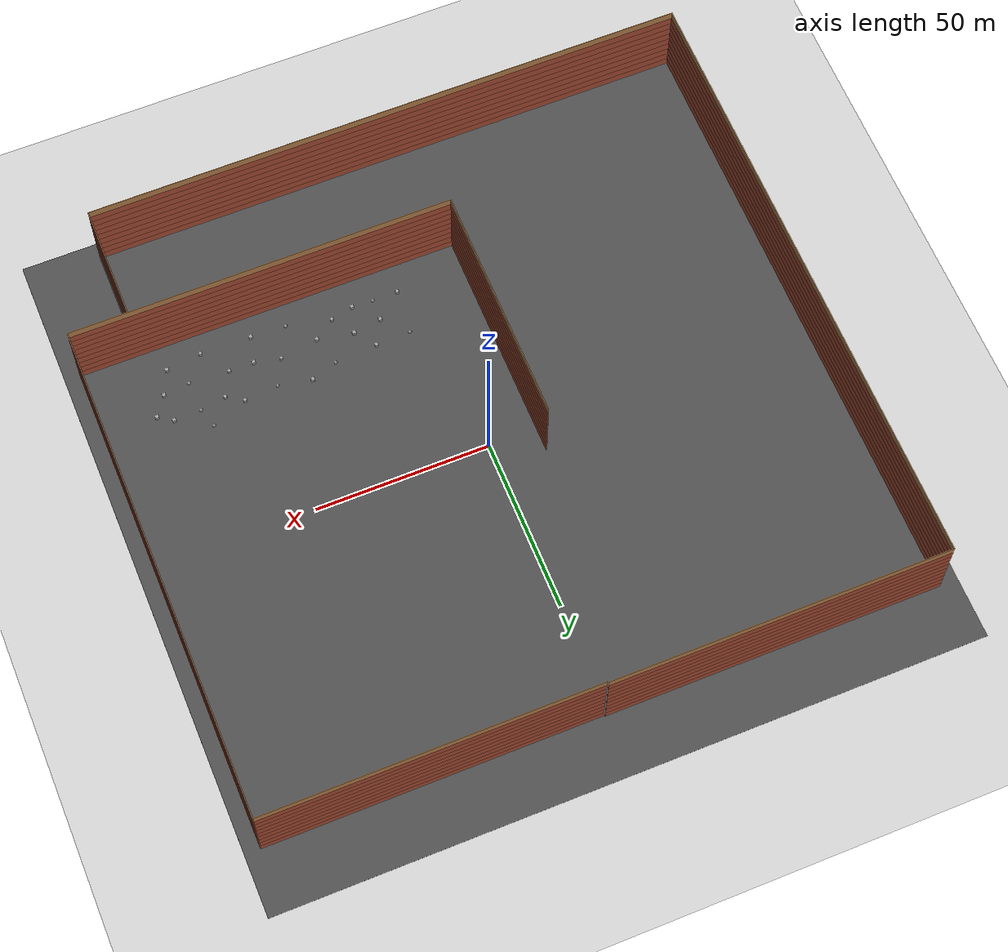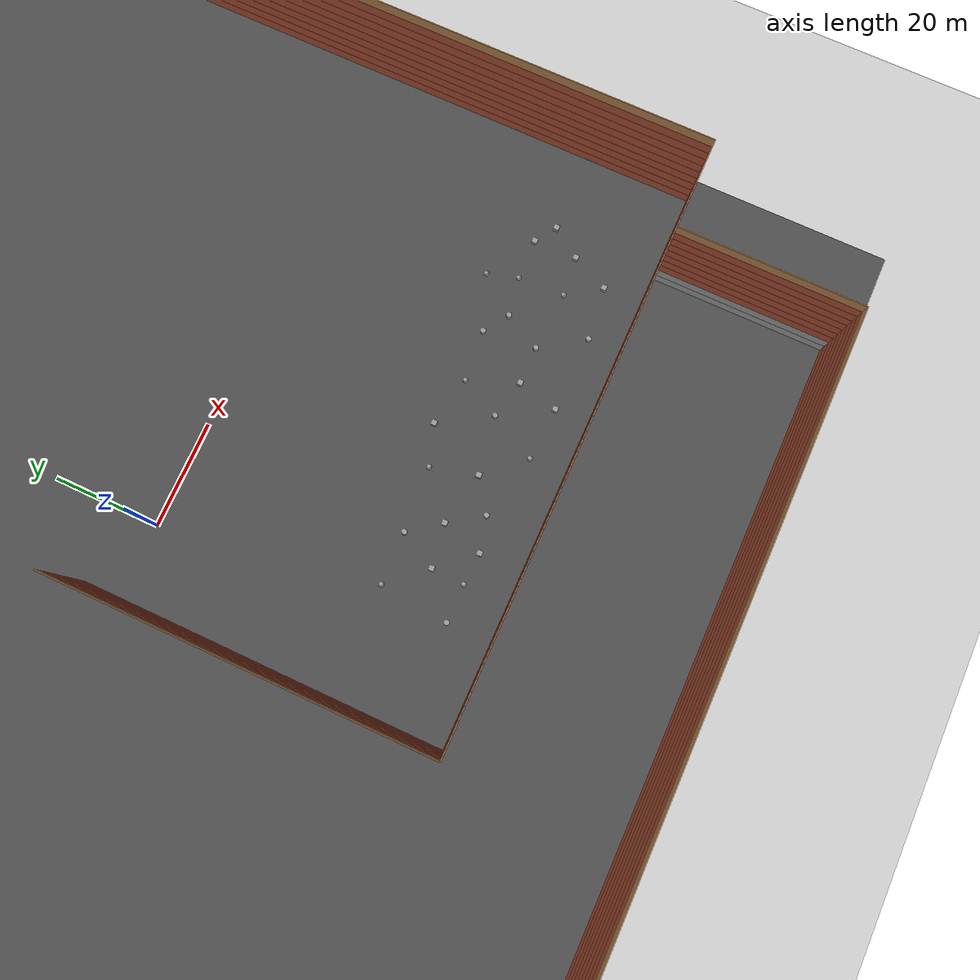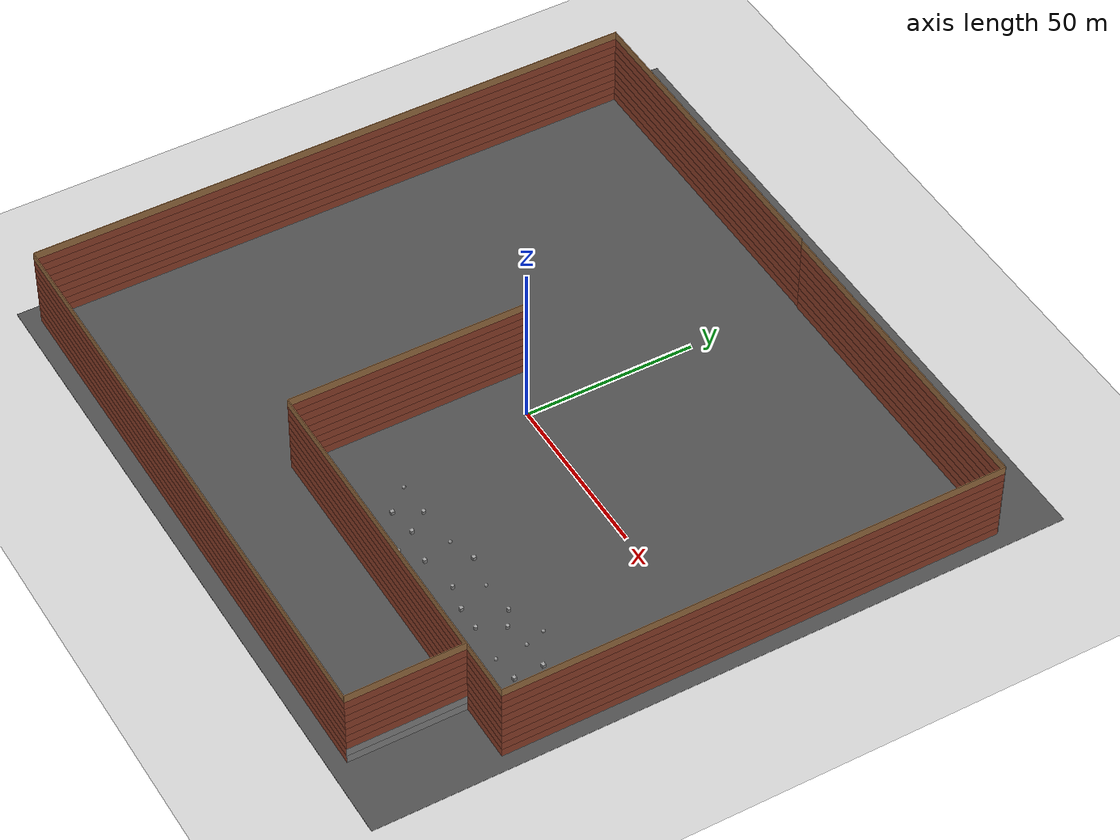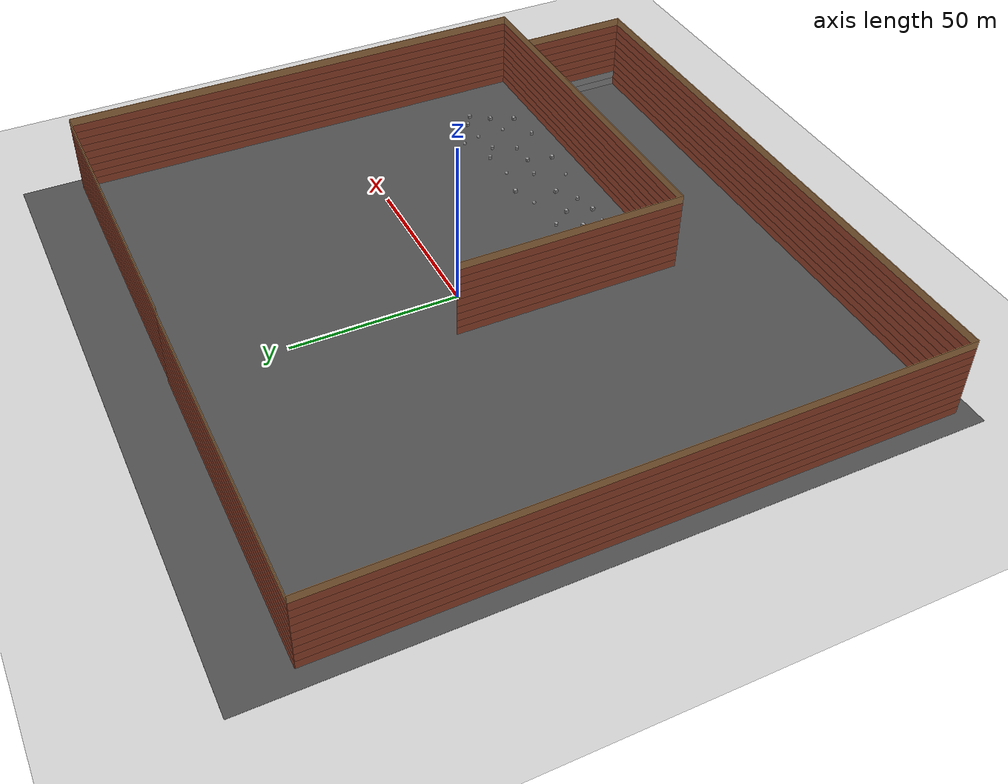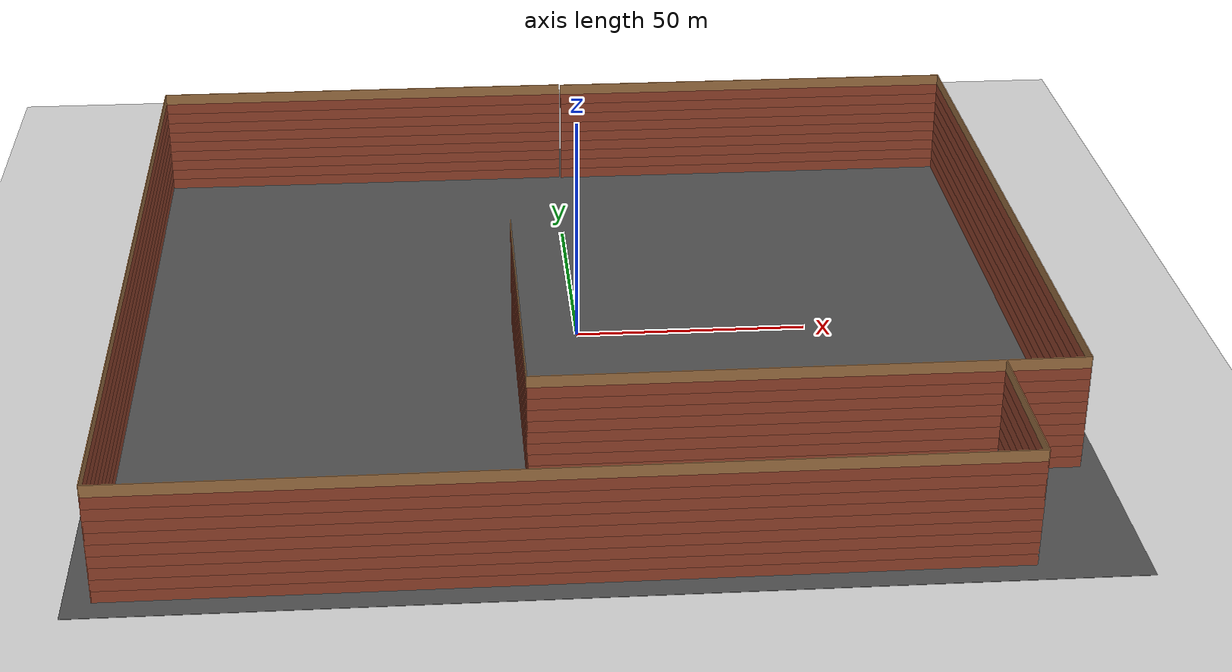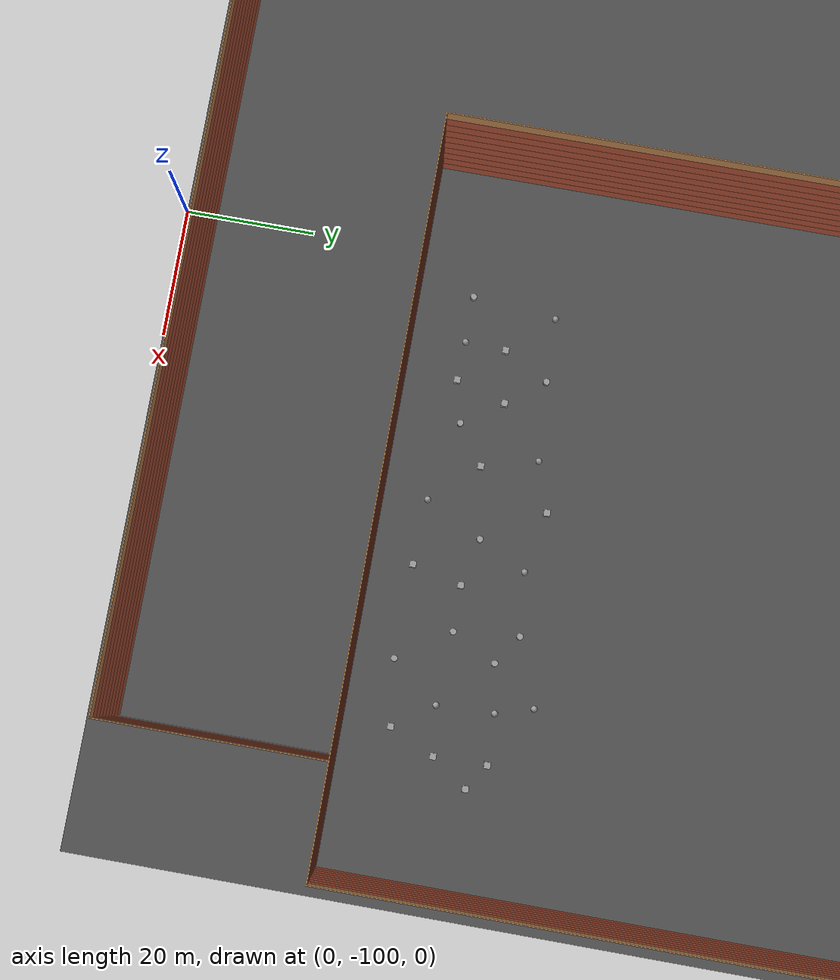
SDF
<sdf version="1.6">
 <world name="default">
  <light name="sun" type="directional">
   <pose>0 0 10 0 -0 0</pose>
   <diffuse>0.8 0.8 0.8 1</diffuse>
   <specular>0.2 0.2 0.2 1</specular>
   <attenuation>
    <range>1000</range>
    <constant>0.9</constant>
    <linear>0.01</linear>
    <quadratic>0.001</quadratic>
   </attenuation>
   <direction>-0.5 0.1 -0.9</direction>
  </light>
  <model name="ground_plane">
   <static>1</static>
   <link name="link">
    <collision name="collision">
     <geometry><plane><normal>0 0 1</normal><size>100 100</size></plane></geometry>
     <surface>
      <contact><collide_bitmask>65535</collide_bitmask></contact>
      <friction><ode><mu>100</mu><mu2>50</mu2></ode></friction>
     </surface>
    </collision>
    <visual name="visual">
     <cast_shadows>0</cast_shadows>
     <geometry><plane><normal>0 0 1</normal><size>100 100</size></plane></geometry>
     <material>
      <script><uri>file://media/materials/scripts/gazebo.material</uri><name>Gazebo/Grey</name></script>
     </material>
    </visual>
   </link>
  </model>
  <model name="asphalt_plane">
   <static>1</static>
   <link name="link">
    <collision name="collision"><geometry><box><size>200 200 0.1</size></box></geometry></collision>
    <visual name="visual">
     <cast_shadows>0</cast_shadows>
     <geometry><box><size>200 200 0.1</size></box></geometry>
     <material>
      <script>
       <uri>model://asphalt_plane/materials/scripts</uri>
       <uri>model://asphalt_plane/materials/textures</uri>
       <name>vrc/asphalt</name>
      </script>
     </material>
    </visual>
   </link>
  </model>
  <physics name="default_physics" default="0" type="ode">
   <ode>
    <solver>
     <type>quick</type>
     <iters>10</iters>
     <sor>1.3</sor>
     <use_dynamic_moi_rescaling>0</use_dynamic_moi_rescaling>
    </solver>
    <constraints>
     <cfm>0</cfm>
     <erp>0.2</erp>
     <contact_max_correcting_vel>100</contact_max_correcting_vel>
     <contact_surface_layer>0.001</contact_surface_layer>
    </constraints>
   </ode>
   <max_step_size>0.004</max_step_size>
   <real_time_factor>1</real_time_factor>
   <real_time_update_rate>250</real_time_update_rate>
  </physics>
  <gravity>0 0 -9.8066</gravity>
  <magnetic_field>6e-06 2.3e-05 -4.2e-05</magnetic_field>
  <atmosphere type="adiabatic"/>
  <scene><ambient>0.4 0.4 0.4 1</ambient><background>0.7 0.7 0.7 1</background><shadows>1</shadows></scene>
  <spherical_coordinates>
   <surface_model>EARTH_WGS84</surface_model>
   <latitude_deg>0</latitude_deg>
   <longitude_deg>0</longitude_deg>
   <elevation>0</elevation>
   <heading_deg>0</heading_deg>
  </spherical_coordinates>
  <model name="Prototipo_paredes">
   <pose>0.475057 -6.28247 0 0 -0 0</pose>
   <link name="Wall_147">
    <collision name="Wall_147_Collision">
     <geometry><box><size>96 0.15 2.5</size></box></geometry>
     <pose>0 0 1.25 0 -0 0</pose>
    </collision>
    <visual name="Wall_147_Visual">
     <pose>0 0 1.25 0 -0 0</pose>
     <geometry><box><size>96 0.15 2.5</size></box></geometry>
     <material>
      <script><uri>file://media/materials/scripts/gazebo.material</uri><name>Gazebo/Bricks</name></script>
      <ambient>1 1 1 1</ambient>
     </material>
     <meta><layer>0</layer></meta>
    </visual>
    <pose>-47.1757 88.925 0 0 -0 3.14159</pose>
   </link>
   <link name="Wall_148">
    <collision name="Wall_148_Collision">
     <geometry><box><size>178 0.15 2.5</size></box></geometry>
     <pose>0 0 1.25 0 -0 0</pose>
    </collision>
    <visual name="Wall_148_Visual">
     <pose>0 0 1.25 0 -0 0</pose>
     <geometry><box><size>178 0.15 2.5</size></box></geometry>
     <material>
      <script><uri>file://media/materials/scripts/gazebo.material</uri><name>Gazebo/Bricks</name></script>
      <ambient>1 1 1 1</ambient>
     </material>
     <meta><layer>0</layer></meta>
    </visual>
    <pose>-95.1007 -3e-06 0 0 -0 -1.5708</pose>
   </link>
   <link name="Wall_149">
    <collision name="Wall_149_Collision">
     <geometry><box><size>173.5 0.15 2.5</size></box></geometry>
     <pose>0 0 1.25 0 -0 0</pose>
    </collision>
    <visual name="Wall_149_Visual">
     <pose>0 0 1.25 0 -0 0</pose>
     <geometry><box><size>173.5 0.15 2.5</size></box></geometry>
     <material>
      <script><uri>file://media/materials/scripts/gazebo.material</uri><name>Gazebo/Bricks</name></script>
      <ambient>1 1 1 1</ambient>
     </material>
     <meta><layer>0</layer></meta>
    </visual>
    <pose>-8.42566 -88.925 0 0 -0 0</pose>
   </link>
   <link name="Wall_150">
    <collision name="Wall_150_Collision">
     <geometry><box><size>33.25 0.15 2.5</size></box></geometry>
     <pose>0 0 1.25 0 -0 0</pose>
    </collision>
    <visual name="Wall_150_Visual">
     <pose>0 0 1.25 0 -0 0</pose>
     <geometry><box><size>33.25 0.15 2.5</size></box></geometry>
     <material>
      <script><uri>file://media/materials/scripts/gazebo.material</uri><name>Gazebo/Grey</name></script>
      <ambient>1 1 1 1</ambient>
     </material>
     <meta><layer>0</layer></meta>
    </visual>
    <pose>78.2493 -72.375 0 0 -0 1.5708</pose>
   </link>
   <link name="Wall_256">
    <collision name="Wall_256_Collision">
     <geometry><box><size>69 0.15 2.5</size></box></geometry>
     <pose>0 0 1.25 0 -0 0</pose>
    </collision>
    <visual name="Wall_256_Visual">
     <pose>0 0 1.25 0 -0 0</pose>
     <geometry><box><size>69 0.15 2.5</size></box></geometry>
     <material>
      <script><uri>file://media/materials/scripts/gazebo.material</uri><name>Gazebo/Bricks</name></script>
      <ambient>1 1 1 1</ambient>
     </material>
     <meta><layer>1</layer></meta>
    </visual>
    <pose>-14.4993 -21.2575 2.5 0 -0 -1.5708</pose>
   </link>
   <link name="Wall_257">
    <collision name="Wall_257_Collision">
     <geometry><box><size>109.75 0.15 2.5</size></box></geometry>
     <pose>0 0 1.25 0 -0 0</pose>
    </collision>
    <visual name="Wall_257_Visual">
     <pose>0 0 1.25 0 -0 0</pose>
     <geometry><box><size>109.75 0.15 2.5</size></box></geometry>
     <material>
      <script><uri>file://media/materials/scripts/gazebo.material</uri><name>Gazebo/Bricks</name></script>
      <ambient>1 1 1 1</ambient>
     </material>
     <meta><layer>1</layer></meta>
    </visual>
    <pose>40.3007 -55.6825 2.5 0 -0 0</pose>
   </link>
   <link name="Wall_258">
    <collision name="Wall_258_Collision">
     <geometry><box><size>144.5 0.15 2.5</size></box></geometry>
     <pose>0 0 1.25 0 -0 0</pose>
    </collision>
    <visual name="Wall_258_Visual">
     <pose>0 0 1.25 0 -0 0</pose>
     <geometry><box><size>144.5 0.15 2.5</size></box></geometry>
     <material>
      <script><uri>file://media/materials/scripts/gazebo.material</uri><name>Gazebo/Bricks</name></script>
      <ambient>1 1 1 1</ambient>
     </material>
     <meta><layer>1</layer></meta>
    </visual>
    <pose>95.1007 16.4925 2.5 0 -0 1.5708</pose>
   </link>
   <link name="Wall_259">
    <collision name="Wall_259_Collision">
     <geometry><box><size>94 0.15 2.5</size></box></geometry>
     <pose>0 0 1.25 0 -0 0</pose>
    </collision>
    <visual name="Wall_259_Visual">
     <pose>0 0 1.25 0 -0 0</pose>
     <geometry><box><size>94 0.15 2.5</size></box></geometry>
     <material>
      <script><uri>file://media/materials/scripts/gazebo.material</uri><name>Gazebo/Bricks</name></script>
      <ambient>1 1 1 1</ambient>
     </material>
     <meta><layer>1</layer></meta>
    </visual>
    <pose>48.1757 88.6675 2.5 0 -0 3.14159</pose>
   </link>
   <link name="Wall_260">
    <collision name="Wall_260_Collision">
     <geometry><box><size>96 0.15 2.5</size></box></geometry>
     <pose>0 0 1.25 0 -0 0</pose>
    </collision>
    <visual name="Wall_260_Visual">
     <pose>0 0 1.25 0 -0 0</pose>
     <geometry><box><size>96 0.15 2.5</size></box></geometry>
     <material>
      <script><uri>file://media/materials/scripts/gazebo.material</uri><name>Gazebo/Bricks</name></script>
      <ambient>1 1 1 1</ambient>
     </material>
     <meta><layer>1</layer></meta>
    </visual>
    <pose>-47.1757 88.925 2.5 0 -0 3.14159</pose>
   </link>
   <link name="Wall_261">
    <collision name="Wall_261_Collision">
     <geometry><box><size>178 0.15 2.5</size></box></geometry>
     <pose>0 0 1.25 0 -0 0</pose>
    </collision>
    <visual name="Wall_261_Visual">
     <pose>0 0 1.25 0 -0 0</pose>
     <geometry><box><size>178 0.15 2.5</size></box></geometry>
     <material>
      <script><uri>file://media/materials/scripts/gazebo.material</uri><name>Gazebo/Bricks</name></script>
      <ambient>1 1 1 1</ambient>
     </material>
     <meta><layer>1</layer></meta>
    </visual>
    <pose>-95.1007 -2e-06 2.5 0 -0 -1.5708</pose>
   </link>
   <link name="Wall_262">
    <collision name="Wall_262_Collision">
     <geometry><box><size>173.5 0.15 2.5</size></box></geometry>
     <pose>0 0 1.25 0 -0 0</pose>
    </collision>
    <visual name="Wall_262_Visual">
     <pose>0 0 1.25 0 -0 0</pose>
     <geometry><box><size>173.5 0.15 2.5</size></box></geometry>
     <material>
      <script><uri>file://media/materials/scripts/gazebo.material</uri><name>Gazebo/Bricks</name></script>
      <ambient>1 1 1 1</ambient>
     </material>
     <meta><layer>1</layer></meta>
    </visual>
    <pose>-8.42566 -88.925 2.5 0 -0 0</pose>
   </link>
   <link name="Wall_263">
    <collision name="Wall_263_Collision">
     <geometry><box><size>33.25 0.15 2.5</size></box></geometry>
     <pose>0 0 1.25 0 -0 0</pose>
    </collision>
    <visual name="Wall_263_Visual">
     <pose>0 0 1.25 0 -0 0</pose>
     <geometry><box><size>33.25 0.15 2.5</size></box></geometry>
     <material>
      <script><uri>file://media/materials/scripts/gazebo.material</uri><name>Gazebo/Grey</name></script>
      <ambient>1 1 1 1</ambient>
     </material>
     <meta><layer>1</layer></meta>
    </visual>
    <pose>78.2493 -72.375 2.5 0 -0 1.5708</pose>
   </link>
   <link name="Wall_264">
    <collision name="Wall_264_Collision">
     <geometry><box><size>69 0.15 2.5</size></box></geometry>
     <pose>0 0 1.25 0 -0 0</pose>
    </collision>
    <visual name="Wall_264_Visual">
     <pose>0 0 1.25 0 -0 0</pose>
     <geometry><box><size>69 0.15 2.5</size></box></geometry>
     <material>
      <script><uri>file://media/materials/scripts/gazebo.material</uri><name>Gazebo/Bricks</name></script>
      <ambient>1 1 1 1</ambient>
     </material>
     <meta><layer>2</layer></meta>
    </visual>
    <pose>-14.4993 -21.2575 5 0 -0 -1.5708</pose>
   </link>
   <link name="Wall_265">
    <collision name="Wall_265_Collision">
     <geometry><box><size>109.75 0.15 2.5</size></box></geometry>
     <pose>0 0 1.25 0 -0 0</pose>
    </collision>
    <visual name="Wall_265_Visual">
     <pose>0 0 1.25 0 -0 0</pose>
     <geometry><box><size>109.75 0.15 2.5</size></box></geometry>
     <material>
      <script><uri>file://media/materials/scripts/gazebo.material</uri><name>Gazebo/Bricks</name></script>
      <ambient>1 1 1 1</ambient>
     </material>
     <meta><layer>2</layer></meta>
    </visual>
    <pose>40.3007 -55.6825 5 0 -0 0</pose>
   </link>
   <link name="Wall_266">
    <collision name="Wall_266_Collision">
     <geometry><box><size>144.5 0.15 2.5</size></box></geometry>
     <pose>0 0 1.25 0 -0 0</pose>
    </collision>
    <visual name="Wall_266_Visual">
     <pose>0 0 1.25 0 -0 0</pose>
     <geometry><box><size>144.5 0.15 2.5</size></box></geometry>
     <material>
      <script><uri>file://media/materials/scripts/gazebo.material</uri><name>Gazebo/Bricks</name></script>
      <ambient>1 1 1 1</ambient>
     </material>
     <meta><layer>2</layer></meta>
    </visual>
    <pose>95.1007 16.4925 5 0 -0 1.5708</pose>
   </link>
   <link name="Wall_267">
    <collision name="Wall_267_Collision">
     <geometry><box><size>94 0.15 2.5</size></box></geometry>
     <pose>0 0 1.25 0 -0 0</pose>
    </collision>
    <visual name="Wall_267_Visual">
     <pose>0 0 1.25 0 -0 0</pose>
     <geometry><box><size>94 0.15 2.5</size></box></geometry>
     <material>
      <script><uri>file://media/materials/scripts/gazebo.material</uri><name>Gazebo/Bricks</name></script>
      <ambient>1 1 1 1</ambient>
     </material>
     <meta><layer>2</layer></meta>
    </visual>
    <pose>48.1757 88.6675 5 0 -0 3.14159</pose>
   </link>
   <link name="Wall_268">
    <collision name="Wall_268_Collision">
     <geometry><box><size>96 0.15 2.5</size></box></geometry>
     <pose>0 0 1.25 0 -0 0</pose>
    </collision>
    <visual name="Wall_268_Visual">
     <pose>0 0 1.25 0 -0 0</pose>
     <geometry><box><size>96 0.15 2.5</size></box></geometry>
     <material>
      <script><uri>file://media/materials/scripts/gazebo.material</uri><name>Gazebo/Bricks</name></script>
      <ambient>1 1 1 1</ambient>
     </material>
     <meta><layer>2</layer></meta>
    </visual>
    <pose>-47.1757 88.925 5 0 -0 3.14159</pose>
   </link>
   <link name="Wall_269">
    <collision name="Wall_269_Collision">
     <geometry><box><size>178 0.15 2.5</size></box></geometry>
     <pose>0 0 1.25 0 -0 0</pose>
    </collision>
    <visual name="Wall_269_Visual">
     <pose>0 0 1.25 0 -0 0</pose>
     <geometry><box><size>178 0.15 2.5</size></box></geometry>
     <material>
      <script><uri>file://media/materials/scripts/gazebo.material</uri><name>Gazebo/Bricks</name></script>
      <ambient>1 1 1 1</ambient>
     </material>
     <meta><layer>2</layer></meta>
    </visual>
    <pose>-95.1007 -2e-06 5 0 -0 -1.5708</pose>
   </link>
   <link name="Wall_270">
    <collision name="Wall_270_Collision">
     <geometry><box><size>173.5 0.15 2.5</size></box></geometry>
     <pose>0 0 1.25 0 -0 0</pose>
    </collision>
    <visual name="Wall_270_Visual">
     <pose>0 0 1.25 0 -0 0</pose>
     <geometry><box><size>173.5 0.15 2.5</size></box></geometry>
     <material>
      <script><uri>file://media/materials/scripts/gazebo.material</uri><name>Gazebo/Bricks</name></script>
      <ambient>1 1 1 1</ambient>
     </material>
     <meta><layer>2</layer></meta>
    </visual>
    <pose>-8.42566 -88.925 5 0 -0 0</pose>
   </link>
   <link name="Wall_271">
    <collision name="Wall_271_Collision">
     <geometry><box><size>33.25 0.15 2.5</size></box></geometry>
     <pose>0 0 1.25 0 -0 0</pose>
    </collision>
    <visual name="Wall_271_Visual">
     <pose>0 0 1.25 0 -0 0</pose>
     <geometry><box><size>33.25 0.15 2.5</size></box></geometry>
     <material>
      <script><uri>file://media/materials/scripts/gazebo.material</uri><name>Gazebo/Bricks</name></script>
      <ambient>1 1 1 1</ambient>
     </material>
     <meta><layer>2</layer></meta>
    </visual>
    <pose>78.2493 -72.375 5 0 -0 1.5708</pose>
   </link>
   <link name="Wall_272">
    <collision name="Wall_272_Collision">
     <geometry><box><size>69 0.15 2.5</size></box></geometry>
     <pose>0 0 1.25 0 -0 0</pose>
    </collision>
    <visual name="Wall_272_Visual">
     <pose>0 0 1.25 0 -0 0</pose>
     <geometry><box><size>69 0.15 2.5</size></box></geometry>
     <material>
      <script><uri>file://media/materials/scripts/gazebo.material</uri><name>Gazebo/Bricks</name></script>
      <ambient>1 1 1 1</ambient>
     </material>
     <meta><layer>3</layer></meta>
    </visual>
    <pose>-14.4993 -21.2575 7.5 0 -0 -1.5708</pose>
   </link>
   <link name="Wall_273">
    <collision name="Wall_273_Collision">
     <geometry><box><size>109.75 0.15 2.5</size></box></geometry>
     <pose>0 0 1.25 0 -0 0</pose>
    </collision>
    <visual name="Wall_273_Visual">
     <pose>0 0 1.25 0 -0 0</pose>
     <geometry><box><size>109.75 0.15 2.5</size></box></geometry>
     <material>
      <script><uri>file://media/materials/scripts/gazebo.material</uri><name>Gazebo/Bricks</name></script>
      <ambient>1 1 1 1</ambient>
     </material>
     <meta><layer>3</layer></meta>
    </visual>
    <pose>40.3007 -55.6825 7.5 0 -0 0</pose>
   </link>
   <link name="Wall_274">
    <collision name="Wall_274_Collision">
     <geometry><box><size>144.5 0.15 2.5</size></box></geometry>
     <pose>0 0 1.25 0 -0 0</pose>
    </collision>
    <visual name="Wall_274_Visual">
     <pose>0 0 1.25 0 -0 0</pose>
     <geometry><box><size>144.5 0.15 2.5</size></box></geometry>
     <material>
      <script><uri>file://media/materials/scripts/gazebo.material</uri><name>Gazebo/Bricks</name></script>
      <ambient>1 1 1 1</ambient>
     </material>
     <meta><layer>3</layer></meta>
    </visual>
    <pose>95.1007 16.4925 7.5 0 -0 1.5708</pose>
   </link>
   <link name="Wall_275">
    <collision name="Wall_275_Collision">
     <geometry><box><size>94 0.15 2.5</size></box></geometry>
     <pose>0 0 1.25 0 -0 0</pose>
    </collision>
    <visual name="Wall_275_Visual">
     <pose>0 0 1.25 0 -0 0</pose>
     <geometry><box><size>94 0.15 2.5</size></box></geometry>
     <material>
      <script><uri>file://media/materials/scripts/gazebo.material</uri><name>Gazebo/Bricks</name></script>
      <ambient>1 1 1 1</ambient>
     </material>
     <meta><layer>3</layer></meta>
    </visual>
    <pose>48.1757 88.6675 7.5 0 -0 3.14159</pose>
   </link>
   <link name="Wall_276">
    <collision name="Wall_276_Collision">
     <geometry><box><size>96 0.15 2.5</size></box></geometry>
     <pose>0 0 1.25 0 -0 0</pose>
    </collision>
    <visual name="Wall_276_Visual">
     <pose>0 0 1.25 0 -0 0</pose>
     <geometry><box><size>96 0.15 2.5</size></box></geometry>
     <material>
      <script><uri>file://media/materials/scripts/gazebo.material</uri><name>Gazebo/Bricks</name></script>
      <ambient>1 1 1 1</ambient>
     </material>
     <meta><layer>3</layer></meta>
    </visual>
    <pose>-47.1757 88.925 7.5 0 -0 3.14159</pose>
   </link>
   <link name="Wall_277">
    <collision name="Wall_277_Collision">
     <geometry><box><size>178 0.15 2.5</size></box></geometry>
     <pose>0 0 1.25 0 -0 0</pose>
    </collision>
    <visual name="Wall_277_Visual">
     <pose>0 0 1.25 0 -0 0</pose>
     <geometry><box><size>178 0.15 2.5</size></box></geometry>
     <material>
      <script><uri>file://media/materials/scripts/gazebo.material</uri><name>Gazebo/Bricks</name></script>
      <ambient>1 1 1 1</ambient>
     </material>
     <meta><layer>3</layer></meta>
    </visual>
    <pose>-95.1007 -2e-06 7.5 0 -0 -1.5708</pose>
   </link>
   <link name="Wall_278">
    <collision name="Wall_278_Collision">
     <geometry><box><size>173.5 0.15 2.5</size></box></geometry>
     <pose>0 0 1.25 0 -0 0</pose>
    </collision>
    <visual name="Wall_278_Visual">
     <pose>0 0 1.25 0 -0 0</pose>
     <geometry><box><size>173.5 0.15 2.5</size></box></geometry>
     <material>
      <script><uri>file://media/materials/scripts/gazebo.material</uri><name>Gazebo/Bricks</name></script>
      <ambient>1 1 1 1</ambient>
     </material>
     <meta><layer>3</layer></meta>
    </visual>
    <pose>-8.42566 -88.925 7.5 0 -0 0</pose>
   </link>
   <link name="Wall_279">
    <collision name="Wall_279_Collision">
     <geometry><box><size>33.25 0.15 2.5</size></box></geometry>
     <pose>0 0 1.25 0 -0 0</pose>
    </collision>
    <visual name="Wall_279_Visual">
     <pose>0 0 1.25 0 -0 0</pose>
     <geometry><box><size>33.25 0.15 2.5</size></box></geometry>
     <material>
      <script><uri>file://media/materials/scripts/gazebo.material</uri><name>Gazebo/Bricks</name></script>
      <ambient>1 1 1 1</ambient>
     </material>
     <meta><layer>3</layer></meta>
    </visual>
    <pose>78.2493 -72.375 7.5 0 -0 1.5708</pose>
   </link>
   <link name="Wall_280">
    <collision name="Wall_280_Collision">
     <geometry><box><size>69 0.15 2.5</size></box></geometry>
     <pose>0 0 1.25 0 -0 0</pose>
    </collision>
    <visual name="Wall_280_Visual">
     <pose>0 0 1.25 0 -0 0</pose>
     <geometry><box><size>69 0.15 2.5</size></box></geometry>
     <material>
      <script><uri>file://media/materials/scripts/gazebo.material</uri><name>Gazebo/Bricks</name></script>
      <ambient>1 1 1 1</ambient>
     </material>
     <meta><layer>4</layer></meta>
    </visual>
    <pose>-14.4993 -21.2575 10 0 -0 -1.5708</pose>
   </link>
   <link name="Wall_281">
    <collision name="Wall_281_Collision">
     <geometry><box><size>109.75 0.15 2.5</size></box></geometry>
     <pose>0 0 1.25 0 -0 0</pose>
    </collision>
    <visual name="Wall_281_Visual">
     <pose>0 0 1.25 0 -0 0</pose>
     <geometry><box><size>109.75 0.15 2.5</size></box></geometry>
     <material>
      <script><uri>file://media/materials/scripts/gazebo.material</uri><name>Gazebo/Bricks</name></script>
      <ambient>1 1 1 1</ambient>
     </material>
     <meta><layer>4</layer></meta>
    </visual>
    <pose>40.3007 -55.6825 10 0 -0 0</pose>
   </link>
   <link name="Wall_282">
    <collision name="Wall_282_Collision">
     <geometry><box><size>144.5 0.15 2.5</size></box></geometry>
     <pose>0 0 1.25 0 -0 0</pose>
    </collision>
    <visual name="Wall_282_Visual">
     <pose>0 0 1.25 0 -0 0</pose>
     <geometry><box><size>144.5 0.15 2.5</size></box></geometry>
     <material>
      <script><uri>file://media/materials/scripts/gazebo.material</uri><name>Gazebo/Bricks</name></script>
      <ambient>1 1 1 1</ambient>
     </material>
     <meta><layer>4</layer></meta>
    </visual>
    <pose>95.1007 16.4925 10 0 -0 1.5708</pose>
   </link>
   <link name="Wall_283">
    <collision name="Wall_283_Collision">
     <geometry><box><size>94 0.15 2.5</size></box></geometry>
     <pose>0 0 1.25 0 -0 0</pose>
    </collision>
    <visual name="Wall_283_Visual">
     <pose>0 0 1.25 0 -0 0</pose>
     <geometry><box><size>94 0.15 2.5</size></box></geometry>
     <material>
      <script><uri>file://media/materials/scripts/gazebo.material</uri><name>Gazebo/Bricks</name></script>
      <ambient>1 1 1 1</ambient>
     </material>
     <meta><layer>4</layer></meta>
    </visual>
    <pose>48.1757 88.6675 10 0 -0 3.14159</pose>
   </link>
   <link name="Wall_284">
    <collision name="Wall_284_Collision">
     <geometry><box><size>96 0.15 2.5</size></box></geometry>
     <pose>0 0 1.25 0 -0 0</pose>
    </collision>
    <visual name="Wall_284_Visual">
     <pose>0 0 1.25 0 -0 0</pose>
     <geometry><box><size>96 0.15 2.5</size></box></geometry>
     <material>
      <script><uri>file://media/materials/scripts/gazebo.material</uri><name>Gazebo/Bricks</name></script>
      <ambient>1 1 1 1</ambient>
     </material>
     <meta><layer>4</layer></meta>
    </visual>
    <pose>-47.1757 88.925 10 0 -0 3.14159</pose>
   </link>
   <link name="Wall_285">
    <collision name="Wall_285_Collision">
     <geometry><box><size>178 0.15 2.5</size></box></geometry>
     <pose>0 0 1.25 0 -0 0</pose>
    </collision>
    <visual name="Wall_285_Visual">
     <pose>0 0 1.25 0 -0 0</pose>
     <geometry><box><size>178 0.15 2.5</size></box></geometry>
     <material>
      <script><uri>file://media/materials/scripts/gazebo.material</uri><name>Gazebo/Bricks</name></script>
      <ambient>1 1 1 1</ambient>
     </material>
     <meta><layer>4</layer></meta>
    </visual>
    <pose>-95.1007 -2e-06 10 0 -0 -1.5708</pose>
   </link>
   <link name="Wall_286">
    <collision name="Wall_286_Collision">
     <geometry><box><size>173.5 0.15 2.5</size></box></geometry>
     <pose>0 0 1.25 0 -0 0</pose>
    </collision>
    <visual name="Wall_286_Visual">
     <pose>0 0 1.25 0 -0 0</pose>
     <geometry><box><size>173.5 0.15 2.5</size></box></geometry>
     <material>
      <script><uri>file://media/materials/scripts/gazebo.material</uri><name>Gazebo/Bricks</name></script>
      <ambient>1 1 1 1</ambient>
     </material>
     <meta><layer>4</layer></meta>
    </visual>
    <pose>-8.42566 -88.925 10 0 -0 0</pose>
   </link>
   <link name="Wall_287">
    <collision name="Wall_287_Collision">
     <geometry><box><size>33.25 0.15 2.5</size></box></geometry>
     <pose>0 0 1.25 0 -0 0</pose>
    </collision>
    <visual name="Wall_287_Visual">
     <pose>0 0 1.25 0 -0 0</pose>
     <geometry><box><size>33.25 0.15 2.5</size></box></geometry>
     <material>
      <script><uri>file://media/materials/scripts/gazebo.material</uri><name>Gazebo/Bricks</name></script>
      <ambient>1 1 1 1</ambient>
     </material>
     <meta><layer>4</layer></meta>
    </visual>
    <pose>78.2493 -72.375 10 0 -0 1.5708</pose>
   </link>
   <link name="Wall_288">
    <collision name="Wall_288_Collision">
     <geometry><box><size>69 0.15 2.5</size></box></geometry>
     <pose>0 0 1.25 0 -0 0</pose>
    </collision>
    <visual name="Wall_288_Visual">
     <pose>0 0 1.25 0 -0 0</pose>
     <geometry><box><size>69 0.15 2.5</size></box></geometry>
     <material>
      <script><uri>file://media/materials/scripts/gazebo.material</uri><name>Gazebo/Bricks</name></script>
      <ambient>1 1 1 1</ambient>
     </material>
     <meta><layer>5</layer></meta>
    </visual>
    <pose>-14.4993 -21.2575 12.5 0 -0 -1.5708</pose>
   </link>
   <link name="Wall_289">
    <collision name="Wall_289_Collision">
     <geometry><box><size>109.75 0.15 2.5</size></box></geometry>
     <pose>0 0 1.25 0 -0 0</pose>
    </collision>
    <visual name="Wall_289_Visual">
     <pose>0 0 1.25 0 -0 0</pose>
     <geometry><box><size>109.75 0.15 2.5</size></box></geometry>
     <material>
      <script><uri>file://media/materials/scripts/gazebo.material</uri><name>Gazebo/Bricks</name></script>
      <ambient>1 1 1 1</ambient>
     </material>
     <meta><layer>5</layer></meta>
    </visual>
    <pose>40.3007 -55.6825 12.5 0 -0 0</pose>
   </link>
   <link name="Wall_290">
    <collision name="Wall_290_Collision">
     <geometry><box><size>144.5 0.15 2.5</size></box></geometry>
     <pose>0 0 1.25 0 -0 0</pose>
    </collision>
    <visual name="Wall_290_Visual">
     <pose>0 0 1.25 0 -0 0</pose>
     <geometry><box><size>144.5 0.15 2.5</size></box></geometry>
     <material>
      <script><uri>file://media/materials/scripts/gazebo.material</uri><name>Gazebo/Bricks</name></script>
      <ambient>1 1 1 1</ambient>
     </material>
     <meta><layer>5</layer></meta>
    </visual>
    <pose>95.1007 16.4925 12.5 0 -0 1.5708</pose>
   </link>
   <link name="Wall_291">
    <collision name="Wall_291_Collision">
     <geometry><box><size>94 0.15 2.5</size></box></geometry>
     <pose>0 0 1.25 0 -0 0</pose>
    </collision>
    <visual name="Wall_291_Visual">
     <pose>0 0 1.25 0 -0 0</pose>
     <geometry><box><size>94 0.15 2.5</size></box></geometry>
     <material>
      <script><uri>file://media/materials/scripts/gazebo.material</uri><name>Gazebo/Bricks</name></script>
      <ambient>1 1 1 1</ambient>
     </material>
     <meta><layer>5</layer></meta>
    </visual>
    <pose>48.1757 88.6675 12.5 0 -0 3.14159</pose>
   </link>
   <link name="Wall_292">
    <collision name="Wall_292_Collision">
     <geometry><box><size>96 0.15 2.5</size></box></geometry>
     <pose>0 0 1.25 0 -0 0</pose>
    </collision>
    <visual name="Wall_292_Visual">
     <pose>0 0 1.25 0 -0 0</pose>
     <geometry><box><size>96 0.15 2.5</size></box></geometry>
     <material>
      <script><uri>file://media/materials/scripts/gazebo.material</uri><name>Gazebo/Bricks</name></script>
      <ambient>1 1 1 1</ambient>
     </material>
     <meta><layer>5</layer></meta>
    </visual>
    <pose>-47.1757 88.925 12.5 0 -0 3.14159</pose>
   </link>
   <link name="Wall_293">
    <collision name="Wall_293_Collision">
     <geometry><box><size>178 0.15 2.5</size></box></geometry>
     <pose>0 0 1.25 0 -0 0</pose>
    </collision>
    <visual name="Wall_293_Visual">
     <pose>0 0 1.25 0 -0 0</pose>
     <geometry><box><size>178 0.15 2.5</size></box></geometry>
     <material>
      <script><uri>file://media/materials/scripts/gazebo.material</uri><name>Gazebo/Bricks</name></script>
      <ambient>1 1 1 1</ambient>
     </material>
     <meta><layer>5</layer></meta>
    </visual>
    <pose>-95.1007 -2e-06 12.5 0 -0 -1.5708</pose>
   </link>
   <link name="Wall_294">
    <collision name="Wall_294_Collision">
     <geometry><box><size>173.5 0.15 2.5</size></box></geometry>
     <pose>0 0 1.25 0 -0 0</pose>
    </collision>
    <visual name="Wall_294_Visual">
     <pose>0 0 1.25 0 -0 0</pose>
     <geometry><box><size>173.5 0.15 2.5</size></box></geometry>
     <material>
      <script><uri>file://media/materials/scripts/gazebo.material</uri><name>Gazebo/Bricks</name></script>
      <ambient>1 1 1 1</ambient>
     </material>
     <meta><layer>5</layer></meta>
    </visual>
    <pose>-8.42566 -88.925 12.5 0 -0 0</pose>
   </link>
   <link name="Wall_295">
    <collision name="Wall_295_Collision">
     <geometry><box><size>33.25 0.15 2.5</size></box></geometry>
     <pose>0 0 1.25 0 -0 0</pose>
    </collision>
    <visual name="Wall_295_Visual">
     <pose>0 0 1.25 0 -0 0</pose>
     <geometry><box><size>33.25 0.15 2.5</size></box></geometry>
     <material>
      <script><uri>file://media/materials/scripts/gazebo.material</uri><name>Gazebo/Bricks</name></script>
      <ambient>1 1 1 1</ambient>
     </material>
     <meta><layer>5</layer></meta>
    </visual>
    <pose>78.2493 -72.375 12.5 0 -0 1.5708</pose>
   </link>
   <link name="Wall_296">
    <collision name="Wall_296_Collision">
     <geometry><box><size>69 0.15 2.5</size></box></geometry>
     <pose>0 0 1.25 0 -0 0</pose>
    </collision>
    <visual name="Wall_296_Visual">
     <pose>0 0 1.25 0 -0 0</pose>
     <geometry><box><size>69 0.15 2.5</size></box></geometry>
     <material>
      <script><uri>file://media/materials/scripts/gazebo.material</uri><name>Gazebo/Bricks</name></script>
      <ambient>1 1 1 1</ambient>
     </material>
     <meta><layer>6</layer></meta>
    </visual>
    <pose>-14.4993 -21.2575 15 0 -0 -1.5708</pose>
   </link>
   <link name="Wall_297">
    <collision name="Wall_297_Collision">
     <geometry><box><size>109.75 0.15 2.5</size></box></geometry>
     <pose>0 0 1.25 0 -0 0</pose>
    </collision>
    <visual name="Wall_297_Visual">
     <pose>0 0 1.25 0 -0 0</pose>
     <geometry><box><size>109.75 0.15 2.5</size></box></geometry>
     <material>
      <script><uri>file://media/materials/scripts/gazebo.material</uri><name>Gazebo/Bricks</name></script>
      <ambient>1 1 1 1</ambient>
     </material>
     <meta><layer>6</layer></meta>
    </visual>
    <pose>40.3007 -55.6825 15 0 -0 0</pose>
   </link>
   <link name="Wall_298">
    <collision name="Wall_298_Collision">
     <geometry><box><size>144.5 0.15 2.5</size></box></geometry>
     <pose>0 0 1.25 0 -0 0</pose>
    </collision>
    <visual name="Wall_298_Visual">
     <pose>0 0 1.25 0 -0 0</pose>
     <geometry><box><size>144.5 0.15 2.5</size></box></geometry>
     <material>
      <script><uri>file://media/materials/scripts/gazebo.material</uri><name>Gazebo/Bricks</name></script>
      <ambient>1 1 1 1</ambient>
     </material>
     <meta><layer>6</layer></meta>
    </visual>
    <pose>95.1007 16.4925 15 0 -0 1.5708</pose>
   </link>
   <link name="Wall_299">
    <collision name="Wall_299_Collision">
     <geometry><box><size>94 0.15 2.5</size></box></geometry>
     <pose>0 0 1.25 0 -0 0</pose>
    </collision>
    <visual name="Wall_299_Visual">
     <pose>0 0 1.25 0 -0 0</pose>
     <geometry><box><size>94 0.15 2.5</size></box></geometry>
     <material>
      <script><uri>file://media/materials/scripts/gazebo.material</uri><name>Gazebo/Bricks</name></script>
      <ambient>1 1 1 1</ambient>
     </material>
     <meta><layer>6</layer></meta>
    </visual>
    <pose>48.1757 88.6675 15 0 -0 3.14159</pose>
   </link>
   <link name="Wall_300">
    <collision name="Wall_300_Collision">
     <geometry><box><size>96 0.15 2.5</size></box></geometry>
     <pose>0 0 1.25 0 -0 0</pose>
    </collision>
    <visual name="Wall_300_Visual">
     <pose>0 0 1.25 0 -0 0</pose>
     <geometry><box><size>96 0.15 2.5</size></box></geometry>
     <material>
      <script><uri>file://media/materials/scripts/gazebo.material</uri><name>Gazebo/Bricks</name></script>
      <ambient>1 1 1 1</ambient>
     </material>
     <meta><layer>6</layer></meta>
    </visual>
    <pose>-47.1757 88.925 15 0 -0 3.14159</pose>
   </link>
   <link name="Wall_301">
    <collision name="Wall_301_Collision">
     <geometry><box><size>178 0.15 2.5</size></box></geometry>
     <pose>0 0 1.25 0 -0 0</pose>
    </collision>
    <visual name="Wall_301_Visual">
     <pose>0 0 1.25 0 -0 0</pose>
     <geometry><box><size>178 0.15 2.5</size></box></geometry>
     <material>
      <script><uri>file://media/materials/scripts/gazebo.material</uri><name>Gazebo/Bricks</name></script>
      <ambient>1 1 1 1</ambient>
     </material>
     <meta><layer>6</layer></meta>
    </visual>
    <pose>-95.1007 -2e-06 15 0 -0 -1.5708</pose>
   </link>
   <link name="Wall_302">
    <collision name="Wall_302_Collision">
     <geometry><box><size>173.5 0.15 2.5</size></box></geometry>
     <pose>0 0 1.25 0 -0 0</pose>
    </collision>
    <visual name="Wall_302_Visual">
     <pose>0 0 1.25 0 -0 0</pose>
     <geometry><box><size>173.5 0.15 2.5</size></box></geometry>
     <material>
      <script><uri>file://media/materials/scripts/gazebo.material</uri><name>Gazebo/Bricks</name></script>
      <ambient>1 1 1 1</ambient>
     </material>
     <meta><layer>6</layer></meta>
    </visual>
    <pose>-8.42566 -88.925 15 0 -0 0</pose>
   </link>
   <link name="Wall_303">
    <collision name="Wall_303_Collision">
     <geometry><box><size>33.25 0.15 2.5</size></box></geometry>
     <pose>0 0 1.25 0 -0 0</pose>
    </collision>
    <visual name="Wall_303_Visual">
     <pose>0 0 1.25 0 -0 0</pose>
     <geometry><box><size>33.25 0.15 2.5</size></box></geometry>
     <material>
      <script><uri>file://media/materials/scripts/gazebo.material</uri><name>Gazebo/Bricks</name></script>
      <ambient>1 1 1 1</ambient>
     </material>
     <meta><layer>6</layer></meta>
    </visual>
    <pose>78.2493 -72.375 15 0 -0 1.5708</pose>
   </link>
   <link name="Wall_304">
    <collision name="Wall_304_Collision">
     <geometry><box><size>69 0.15 2.5</size></box></geometry>
     <pose>0 0 1.25 0 -0 0</pose>
    </collision>
    <visual name="Wall_304_Visual">
     <pose>0 0 1.25 0 -0 0</pose>
     <geometry><box><size>69 0.15 2.5</size></box></geometry>
     <material>
      <script><uri>file://media/materials/scripts/gazebo.material</uri><name>Gazebo/Bricks</name></script>
      <ambient>1 1 1 1</ambient>
     </material>
     <meta><layer>7</layer></meta>
    </visual>
    <pose>-14.4993 -21.2575 17.5 0 -0 -1.5708</pose>
   </link>
   <link name="Wall_305">
    <collision name="Wall_305_Collision">
     <geometry><box><size>109.75 0.15 2.5</size></box></geometry>
     <pose>0 0 1.25 0 -0 0</pose>
    </collision>
    <visual name="Wall_305_Visual">
     <pose>0 0 1.25 0 -0 0</pose>
     <geometry><box><size>109.75 0.15 2.5</size></box></geometry>
     <material>
      <script><uri>file://media/materials/scripts/gazebo.material</uri><name>Gazebo/Bricks</name></script>
      <ambient>1 1 1 1</ambient>
     </material>
     <meta><layer>7</layer></meta>
    </visual>
    <pose>40.3007 -55.6825 17.5 0 -0 0</pose>
   </link>
   <link name="Wall_306">
    <collision name="Wall_306_Collision">
     <geometry><box><size>144.5 0.15 2.5</size></box></geometry>
     <pose>0 0 1.25 0 -0 0</pose>
    </collision>
    <visual name="Wall_306_Visual">
     <pose>0 0 1.25 0 -0 0</pose>
     <geometry><box><size>144.5 0.15 2.5</size></box></geometry>
     <material>
      <script><uri>file://media/materials/scripts/gazebo.material</uri><name>Gazebo/Bricks</name></script>
      <ambient>1 1 1 1</ambient>
     </material>
     <meta><layer>7</layer></meta>
    </visual>
    <pose>95.1007 16.4925 17.5 0 -0 1.5708</pose>
   </link>
   <link name="Wall_307">
    <collision name="Wall_307_Collision">
     <geometry><box><size>94 0.15 2.5</size></box></geometry>
     <pose>0 0 1.25 0 -0 0</pose>
    </collision>
    <visual name="Wall_307_Visual">
     <pose>0 0 1.25 0 -0 0</pose>
     <geometry><box><size>94 0.15 2.5</size></box></geometry>
     <material>
      <script><uri>file://media/materials/scripts/gazebo.material</uri><name>Gazebo/Bricks</name></script>
      <ambient>1 1 1 1</ambient>
     </material>
     <meta><layer>7</layer></meta>
    </visual>
    <pose>48.1757 88.6675 17.5 0 -0 3.14159</pose>
   </link>
   <link name="Wall_308">
    <collision name="Wall_308_Collision">
     <geometry><box><size>96 0.15 2.5</size></box></geometry>
     <pose>0 0 1.25 0 -0 0</pose>
    </collision>
    <visual name="Wall_308_Visual">
     <pose>0 0 1.25 0 -0 0</pose>
     <geometry><box><size>96 0.15 2.5</size></box></geometry>
     <material>
      <script><uri>file://media/materials/scripts/gazebo.material</uri><name>Gazebo/Bricks</name></script>
      <ambient>1 1 1 1</ambient>
     </material>
     <meta><layer>7</layer></meta>
    </visual>
    <pose>-47.1757 88.925 17.5 0 -0 3.14159</pose>
   </link>
   <link name="Wall_309">
    <collision name="Wall_309_Collision">
     <geometry><box><size>178 0.15 2.5</size></box></geometry>
     <pose>0 0 1.25 0 -0 0</pose>
    </collision>
    <visual name="Wall_309_Visual">
     <pose>0 0 1.25 0 -0 0</pose>
     <geometry><box><size>178 0.15 2.5</size></box></geometry>
     <material>
      <script><uri>file://media/materials/scripts/gazebo.material</uri><name>Gazebo/Bricks</name></script>
      <ambient>1 1 1 1</ambient>
     </material>
     <meta><layer>7</layer></meta>
    </visual>
    <pose>-95.1007 -2e-06 17.5 0 -0 -1.5708</pose>
   </link>
   <link name="Wall_310">
    <collision name="Wall_310_Collision">
     <geometry><box><size>173.5 0.15 2.5</size></box></geometry>
     <pose>0 0 1.25 0 -0 0</pose>
    </collision>
    <visual name="Wall_310_Visual">
     <pose>0 0 1.25 0 -0 0</pose>
     <geometry><box><size>173.5 0.15 2.5</size></box></geometry>
     <material>
      <script><uri>file://media/materials/scripts/gazebo.material</uri><name>Gazebo/Bricks</name></script>
      <ambient>1 1 1 1</ambient>
     </material>
     <meta><layer>7</layer></meta>
    </visual>
    <pose>-8.42566 -88.925 17.5 0 -0 0</pose>
   </link>
   <link name="Wall_311">
    <collision name="Wall_311_Collision">
     <geometry><box><size>33.25 0.15 2.5</size></box></geometry>
     <pose>0 0 1.25 0 -0 0</pose>
    </collision>
    <visual name="Wall_311_Visual">
     <pose>0 0 1.25 0 -0 0</pose>
     <geometry><box><size>33.25 0.15 2.5</size></box></geometry>
     <material>
      <script><uri>file://media/materials/scripts/gazebo.material</uri><name>Gazebo/Bricks</name></script>
      <ambient>1 1 1 1</ambient>
     </material>
     <meta><layer>7</layer></meta>
    </visual>
    <pose>78.2493 -72.375 17.5 0 -0 1.5708</pose>
   </link>
   <link name="Wall_312">
    <collision name="Wall_312_Collision">
     <geometry><box><size>69 0.15 2.5</size></box></geometry>
     <pose>0 0 1.25 0 -0 0</pose>
    </collision>
    <visual name="Wall_312_Visual">
     <pose>0 0 1.25 0 -0 0</pose>
     <geometry><box><size>69 0.15 2.5</size></box></geometry>
     <material>
      <script><uri>file://media/materials/scripts/gazebo.material</uri><name>Gazebo/Bricks</name></script>
      <ambient>1 1 1 1</ambient>
     </material>
     <meta><layer>8</layer></meta>
    </visual>
    <pose>-14.4993 -21.2575 20 0 -0 -1.5708</pose>
   </link>
   <link name="Wall_313">
    <collision name="Wall_313_Collision">
     <geometry><box><size>109.75 0.15 2.5</size></box></geometry>
     <pose>0 0 1.25 0 -0 0</pose>
    </collision>
    <visual name="Wall_313_Visual">
     <pose>0 0 1.25 0 -0 0</pose>
     <geometry><box><size>109.75 0.15 2.5</size></box></geometry>
     <material>
      <script><uri>file://media/materials/scripts/gazebo.material</uri><name>Gazebo/Bricks</name></script>
      <ambient>1 1 1 1</ambient>
     </material>
     <meta><layer>8</layer></meta>
    </visual>
    <pose>40.3007 -55.6825 20 0 -0 0</pose>
   </link>
   <link name="Wall_314">
    <collision name="Wall_314_Collision">
     <geometry><box><size>144.5 0.15 2.5</size></box></geometry>
     <pose>0 0 1.25 0 -0 0</pose>
    </collision>
    <visual name="Wall_314_Visual">
     <pose>0 0 1.25 0 -0 0</pose>
     <geometry><box><size>144.5 0.15 2.5</size></box></geometry>
     <material>
      <script><uri>file://media/materials/scripts/gazebo.material</uri><name>Gazebo/Bricks</name></script>
      <ambient>1 1 1 1</ambient>
     </material>
     <meta><layer>8</layer></meta>
    </visual>
    <pose>95.1007 16.4925 20 0 -0 1.5708</pose>
   </link>
   <link name="Wall_315">
    <collision name="Wall_315_Collision">
     <geometry><box><size>94 0.15 2.5</size></box></geometry>
     <pose>0 0 1.25 0 -0 0</pose>
    </collision>
    <visual name="Wall_315_Visual">
     <pose>0 0 1.25 0 -0 0</pose>
     <geometry><box><size>94 0.15 2.5</size></box></geometry>
     <material>
      <script><uri>file://media/materials/scripts/gazebo.material</uri><name>Gazebo/Bricks</name></script>
      <ambient>1 1 1 1</ambient>
     </material>
     <meta><layer>8</layer></meta>
    </visual>
    <pose>48.1757 88.6675 20 0 -0 3.14159</pose>
   </link>
   <link name="Wall_316">
    <collision name="Wall_316_Collision">
     <geometry><box><size>96 0.15 2.5</size></box></geometry>
     <pose>0 0 1.25 0 -0 0</pose>
    </collision>
    <visual name="Wall_316_Visual">
     <pose>0 0 1.25 0 -0 0</pose>
     <geometry><box><size>96 0.15 2.5</size></box></geometry>
     <material>
      <script><uri>file://media/materials/scripts/gazebo.material</uri><name>Gazebo/Bricks</name></script>
      <ambient>1 1 1 1</ambient>
     </material>
     <meta><layer>8</layer></meta>
    </visual>
    <pose>-47.1757 88.925 20 0 -0 3.14159</pose>
   </link>
   <link name="Wall_317">
    <collision name="Wall_317_Collision">
     <geometry><box><size>178 0.15 2.5</size></box></geometry>
     <pose>0 0 1.25 0 -0 0</pose>
    </collision>
    <visual name="Wall_317_Visual">
     <pose>0 0 1.25 0 -0 0</pose>
     <geometry><box><size>178 0.15 2.5</size></box></geometry>
     <material>
      <script><uri>file://media/materials/scripts/gazebo.material</uri><name>Gazebo/Bricks</name></script>
      <ambient>1 1 1 1</ambient>
     </material>
     <meta><layer>8</layer></meta>
    </visual>
    <pose>-95.1007 -2e-06 20 0 -0 -1.5708</pose>
   </link>
   <link name="Wall_318">
    <collision name="Wall_318_Collision">
     <geometry><box><size>173.5 0.15 2.5</size></box></geometry>
     <pose>0 0 1.25 0 -0 0</pose>
    </collision>
    <visual name="Wall_318_Visual">
     <pose>0 0 1.25 0 -0 0</pose>
     <geometry><box><size>173.5 0.15 2.5</size></box></geometry>
     <material>
      <script><uri>file://media/materials/scripts/gazebo.material</uri><name>Gazebo/Bricks</name></script>
      <ambient>1 1 1 1</ambient>
     </material>
     <meta><layer>8</layer></meta>
    </visual>
    <pose>-8.42566 -88.925 20 0 -0 0</pose>
   </link>
   <link name="Wall_319">
    <collision name="Wall_319_Collision">
     <geometry><box><size>33.25 0.15 2.5</size></box></geometry>
     <pose>0 0 1.25 0 -0 0</pose>
    </collision>
    <visual name="Wall_319_Visual">
     <pose>0 0 1.25 0 -0 0</pose>
     <geometry><box><size>33.25 0.15 2.5</size></box></geometry>
     <material>
      <script><uri>file://media/materials/scripts/gazebo.material</uri><name>Gazebo/Bricks</name></script>
      <ambient>1 1 1 1</ambient>
     </material>
     <meta><layer>8</layer></meta>
    </visual>
    <pose>78.2493 -72.375 20 0 -0 1.5708</pose>
   </link>
   <link name="Wall_320">
    <collision name="Wall_320_Collision">
     <geometry><box><size>69 0.15 2.5</size></box></geometry>
     <pose>0 0 1.25 0 -0 0</pose>
    </collision>
    <visual name="Wall_320_Visual">
     <pose>0 0 1.25 0 -0 0</pose>
     <geometry><box><size>69 0.15 2.5</size></box></geometry>
     <material>
      <script><uri>file://media/materials/scripts/gazebo.material</uri><name>Gazebo/Wood</name></script>
      <ambient>1 1 1 1</ambient>
     </material>
     <meta><layer>9</layer></meta>
    </visual>
    <pose>-14.4993 -21.2575 22.5 0 -0 -1.5708</pose>
   </link>
   <link name="Wall_321">
    <collision name="Wall_321_Collision">
     <geometry><box><size>109.75 0.15 2.5</size></box></geometry>
     <pose>0 0 1.25 0 -0 0</pose>
    </collision>
    <visual name="Wall_321_Visual">
     <pose>0 0 1.25 0 -0 0</pose>
     <geometry><box><size>109.75 0.15 2.5</size></box></geometry>
     <material>
      <script><uri>file://media/materials/scripts/gazebo.material</uri><name>Gazebo/Wood</name></script>
      <ambient>1 1 1 1</ambient>
     </material>
     <meta><layer>9</layer></meta>
    </visual>
    <pose>40.3007 -55.6825 22.5 0 -0 0</pose>
   </link>
   <link name="Wall_322">
    <collision name="Wall_322_Collision">
     <geometry><box><size>144.5 0.15 2.5</size></box></geometry>
     <pose>0 0 1.25 0 -0 0</pose>
    </collision>
    <visual name="Wall_322_Visual">
     <pose>0 0 1.25 0 -0 0</pose>
     <geometry><box><size>144.5 0.15 2.5</size></box></geometry>
     <material>
      <script><uri>file://media/materials/scripts/gazebo.material</uri><name>Gazebo/Wood</name></script>
      <ambient>1 1 1 1</ambient>
     </material>
     <meta><layer>9</layer></meta>
    </visual>
    <pose>95.1007 16.4925 22.5 0 -0 1.5708</pose>
   </link>
   <link name="Wall_323">
    <collision name="Wall_323_Collision">
     <geometry><box><size>94 0.15 2.5</size></box></geometry>
     <pose>0 0 1.25 0 -0 0</pose>
    </collision>
    <visual name="Wall_323_Visual">
     <pose>0 0 1.25 0 -0 0</pose>
     <geometry><box><size>94 0.15 2.5</size></box></geometry>
     <material>
      <script><uri>file://media/materials/scripts/gazebo.material</uri><name>Gazebo/Wood</name></script>
      <ambient>1 1 1 1</ambient>
     </material>
     <meta><layer>9</layer></meta>
    </visual>
    <pose>48.1757 88.6675 22.5 0 -0 3.14159</pose>
   </link>
   <link name="Wall_324">
    <collision name="Wall_324_Collision">
     <geometry><box><size>96 0.15 2.5</size></box></geometry>
     <pose>0 0 1.25 0 -0 0</pose>
    </collision>
    <visual name="Wall_324_Visual">
     <pose>0 0 1.25 0 -0 0</pose>
     <geometry><box><size>96 0.15 2.5</size></box></geometry>
     <material>
      <script><uri>file://media/materials/scripts/gazebo.material</uri><name>Gazebo/Wood</name></script>
      <ambient>1 1 1 1</ambient>
     </material>
     <meta><layer>9</layer></meta>
    </visual>
    <pose>-47.1757 88.925 22.5 0 -0 3.14159</pose>
   </link>
   <link name="Wall_325">
    <collision name="Wall_325_Collision">
     <geometry><box><size>178 0.15 2.5</size></box></geometry>
     <pose>0 0 1.25 0 -0 0</pose>
    </collision>
    <visual name="Wall_325_Visual">
     <pose>0 0 1.25 0 -0 0</pose>
     <geometry><box><size>178 0.15 2.5</size></box></geometry>
     <material>
      <script><uri>file://media/materials/scripts/gazebo.material</uri><name>Gazebo/Wood</name></script>
      <ambient>1 1 1 1</ambient>
     </material>
     <meta><layer>9</layer></meta>
    </visual>
    <pose>-95.1007 -2e-06 22.5 0 -0 -1.5708</pose>
   </link>
   <link name="Wall_326">
    <collision name="Wall_326_Collision">
     <geometry><box><size>173.5 0.15 2.5</size></box></geometry>
     <pose>0 0 1.25 0 -0 0</pose>
    </collision>
    <visual name="Wall_326_Visual">
     <pose>0 0 1.25 0 -0 0</pose>
     <geometry><box><size>173.5 0.15 2.5</size></box></geometry>
     <material>
      <script><uri>file://media/materials/scripts/gazebo.material</uri><name>Gazebo/Wood</name></script>
      <ambient>1 1 1 1</ambient>
     </material>
     <meta><layer>9</layer></meta>
    </visual>
    <pose>-8.42566 -88.925 22.5 0 -0 0</pose>
   </link>
   <link name="Wall_327">
    <collision name="Wall_327_Collision">
     <geometry><box><size>33.25 0.15 2.5</size></box></geometry>
     <pose>0 0 1.25 0 -0 0</pose>
    </collision>
    <visual name="Wall_327_Visual">
     <pose>0 0 1.25 0 -0 0</pose>
     <geometry><box><size>33.25 0.15 2.5</size></box></geometry>
     <material>
      <script><uri>file://media/materials/scripts/gazebo.material</uri><name>Gazebo/Wood</name></script>
      <ambient>1 1 1 1</ambient>
     </material>
     <meta><layer>9</layer></meta>
    </visual>
    <pose>78.2493 -72.375 22.5 0 -0 1.5708</pose>
   </link>
   <link name="Wall_77">
    <collision name="Wall_77_Collision">
     <geometry><box><size>69 0.15 2.5</size></box></geometry>
     <pose>0 0 1.25 0 -0 0</pose>
    </collision>
    <visual name="Wall_77_Visual">
     <pose>0 0 1.25 0 -0 0</pose>
     <geometry><box><size>69 0.15 2.5</size></box></geometry>
     <material>
      <script><uri>file://media/materials/scripts/gazebo.material</uri><name>Gazebo/Bricks</name></script>
      <ambient>1 1 1 1</ambient>
     </material>
     <meta><layer>0</layer></meta>
    </visual>
    <pose>-14.4993 -21.2575 0 0 -0 -1.5708</pose>
   </link>
   <link name="Wall_78">
    <collision name="Wall_78_Collision">
     <geometry><box><size>109.75 0.15 2.5</size></box></geometry>
     <pose>0 0 1.25 0 -0 0</pose>
    </collision>
    <visual name="Wall_78_Visual">
     <pose>0 0 1.25 0 -0 0</pose>
     <geometry><box><size>109.75 0.15 2.5</size></box></geometry>
     <material>
      <script><uri>file://media/materials/scripts/gazebo.material</uri><name>Gazebo/Bricks</name></script>
      <ambient>1 1 1 1</ambient>
     </material>
     <meta><layer>0</layer></meta>
    </visual>
    <pose>40.3007 -55.6825 0 0 -0 0</pose>
   </link>
   <link name="Wall_79">
    <collision name="Wall_79_Collision">
     <geometry><box><size>144.5 0.15 2.5</size></box></geometry>
     <pose>0 0 1.25 0 -0 0</pose>
    </collision>
    <visual name="Wall_79_Visual">
     <pose>0 0 1.25 0 -0 0</pose>
     <geometry><box><size>144.5 0.15 2.5</size></box></geometry>
     <material>
      <script><uri>file://media/materials/scripts/gazebo.material</uri><name>Gazebo/Bricks</name></script>
      <ambient>1 1 1 1</ambient>
     </material>
     <meta><layer>0</layer></meta>
    </visual>
    <pose>95.1007 16.4925 0 0 -0 1.5708</pose>
   </link>
   <link name="Wall_80">
    <collision name="Wall_80_Collision">
     <geometry><box><size>94 0.15 2.5</size></box></geometry>
     <pose>0 0 1.25 0 -0 0</pose>
    </collision>
    <visual name="Wall_80_Visual">
     <pose>0 0 1.25 0 -0 0</pose>
     <geometry><box><size>94 0.15 2.5</size></box></geometry>
     <material>
      <script><uri>file://media/materials/scripts/gazebo.material</uri><name>Gazebo/Bricks</name></script>
      <ambient>1 1 1 1</ambient>
     </material>
     <meta><layer>0</layer></meta>
    </visual>
    <pose>48.1757 88.6675 0 0 -0 3.14159</pose>
   </link>
   <static>1</static>
  </model>
  <model name="unit_box">
   <pose>76.3165 -47.5509 0.549946 0.000103 -1e-06 -0.001393</pose>
   <link name="link">
    <inertial>
     <mass>1</mass>
     <inertia>
      <ixx>0.166667</ixx>
      <ixy>0</ixy>
      <ixz>0</ixz>
      <iyy>0.166667</iyy>
      <iyz>0</iyz>
      <izz>0.166667</izz>
     </inertia>
    </inertial>
    <collision name="collision"><geometry><box><size>1 1 1</size></box></geometry></collision>
    <visual name="visual">
     <geometry><box><size>1 1 1</size></box></geometry>
     <material>
      <script><name>Gazebo/Grey</name><uri>file://media/materials/scripts/gazebo.material</uri></script>
     </material>
    </visual>
   </link>
  </model>
  <model name="unit_sphere">
   <pose>68.7331 -48.415 0.55 0 -0 0</pose>
   <link name="link">
    <inertial>
     <mass>1</mass>
     <inertia><ixx>0.1</ixx><ixy>0</ixy><ixz>0</ixz><iyy>0.1</iyy><iyz>0</iyz><izz>0.1</izz></inertia>
    </inertial>
    <collision name="collision"><geometry><sphere><radius>0.5</radius></sphere></geometry></collision>
    <visual name="visual">
     <geometry><sphere><radius>0.5</radius></sphere></geometry>
     <material>
      <script><name>Gazebo/Grey</name><uri>file://media/materials/scripts/gazebo.material</uri></script>
     </material>
    </visual>
   </link>
  </model>
  <model name="unit_cylinder">
   <pose>57.34 -47.7885 0.550071 0.000142 5.5e-05 -0.00137</pose>
   <link name="link">
    <inertial>
     <mass>1</mass>
     <inertia><ixx>0.145833</ixx><ixy>0</ixy><ixz>0</ixz><iyy>0.145833</iyy><iyz>0</iyz><izz>0.125</izz></inertia>
    </inertial>
    <collision name="collision">
     <geometry><cylinder><radius>0.5</radius><length>1</length></cylinder></geometry>
    </collision>
    <visual name="visual">
     <geometry><cylinder><radius>0.5</radius><length>1</length></cylinder></geometry>
     <material>
      <script><name>Gazebo/Grey</name><uri>file://media/materials/scripts/gazebo.material</uri></script>
     </material>
    </visual>
   </link>
  </model>
  <model name="unit_sphere_0">
   <pose>66.6909 -33.7382 0.55 0 -0 0</pose>
   <link name="link">
    <inertial>
     <mass>1</mass>
     <inertia><ixx>0.1</ixx><ixy>0</ixy><ixz>0</ixz><iyy>0.1</iyy><iyz>0</iyz><izz>0.1</izz></inertia>
    </inertial>
    <collision name="collision"><geometry><sphere><radius>0.5</radius></sphere></geometry></collision>
    <visual name="visual">
     <geometry><sphere><radius>0.5</radius></sphere></geometry>
     <material>
      <script><name>Gazebo/Grey</name><uri>file://media/materials/scripts/gazebo.material</uri></script>
     </material>
    </visual>
   </link>
  </model>
  <model name="unit_box_0">
   <pose>76.2003 -39.2997 0.549946 0.000103 -1e-06 -0.001213</pose>
   <link name="link">
    <inertial>
     <mass>1</mass>
     <inertia>
      <ixx>0.166667</ixx>
      <ixy>0</ixy>
      <ixz>0</ixz>
      <iyy>0.166667</iyy>
      <iyz>0</iyz>
      <izz>0.166667</izz>
     </inertia>
    </inertial>
    <collision name="collision"><geometry><box><size>1 1 1</size></box></geometry></collision>
    <visual name="visual">
     <geometry><box><size>1 1 1</size></box></geometry>
     <material>
      <script><name>Gazebo/Grey</name><uri>file://media/materials/scripts/gazebo.material</uri></script>
     </material>
    </visual>
   </link>
  </model>
  <model name="unit_cylinder_0">
   <pose>56.3174 -37.7063 0.54998 -4.7e-05 -1.9e-05 -0.001073</pose>
   <link name="link">
    <inertial>
     <mass>1</mass>
     <inertia><ixx>0.145833</ixx><ixy>0</ixy><ixz>0</ixz><iyy>0.145833</iyy><iyz>0</iyz><izz>0.125</izz></inertia>
    </inertial>
    <collision name="collision">
     <geometry><cylinder><radius>0.5</radius><length>1</length></cylinder></geometry>
    </collision>
    <visual name="visual">
     <geometry><cylinder><radius>0.5</radius><length>1</length></cylinder></geometry>
     <material>
      <script><name>Gazebo/Grey</name><uri>file://media/materials/scripts/gazebo.material</uri></script>
     </material>
    </visual>
   </link>
  </model>
  <model name="unit_sphere_1">
   <pose>29.3397 -39.3263 0.55 0 -0 0</pose>
   <link name="link">
    <inertial>
     <mass>1</mass>
     <inertia><ixx>0.1</ixx><ixy>0</ixy><ixz>0</ixz><iyy>0.1</iyy><iyz>0</iyz><izz>0.1</izz></inertia>
    </inertial>
    <collision name="collision"><geometry><sphere><radius>0.5</radius></sphere></geometry></collision>
    <visual name="visual">
     <geometry><sphere><radius>0.5</radius></sphere></geometry>
     <material>
      <script><name>Gazebo/Grey</name><uri>file://media/materials/scripts/gazebo.material</uri></script>
     </material>
    </visual>
   </link>
  </model>
  <model name="unit_box_1">
   <pose>37.0064 -36.8023 0.550003 1.8e-05 5e-06 -0.001078</pose>
   <link name="link">
    <inertial>
     <mass>1</mass>
     <inertia>
      <ixx>0.166667</ixx>
      <ixy>0</ixy>
      <ixz>0</ixz>
      <iyy>0.166667</iyy>
      <iyz>0</iyz>
      <izz>0.166667</izz>
     </inertia>
    </inertial>
    <collision name="collision"><geometry><box><size>1 1 1</size></box></geometry></collision>
    <visual name="visual">
     <geometry><box><size>1 1 1</size></box></geometry>
     <material>
      <script><name>Gazebo/Grey</name><uri>file://media/materials/scripts/gazebo.material</uri></script>
     </material>
    </visual>
   </link>
  </model>
  <model name="unit_cylinder_1">
   <pose>42.769 -46.1833 0.550018 -3.6e-05 -9e-06 -0.001094</pose>
   <link name="link">
    <inertial>
     <mass>1</mass>
     <inertia><ixx>0.145833</ixx><ixy>0</ixy><ixz>0</ixz><iyy>0.145833</iyy><iyz>0</iyz><izz>0.125</izz></inertia>
    </inertial>
    <collision name="collision">
     <geometry><cylinder><radius>0.5</radius><length>1</length></cylinder></geometry>
    </collision>
    <visual name="visual">
     <geometry><cylinder><radius>0.5</radius><length>1</length></cylinder></geometry>
     <material>
      <script><name>Gazebo/Grey</name><uri>file://media/materials/scripts/gazebo.material</uri></script>
     </material>
    </visual>
   </link>
  </model>
  <model name="unit_box_2">
   <pose>21.3912 -46.0549 0.550001 -2.2e-05 -4e-06 -0.000988</pose>
   <link name="link">
    <inertial>
     <mass>1</mass>
     <inertia>
      <ixx>0.166667</ixx>
      <ixy>0</ixy>
      <ixz>0</ixz>
      <iyy>0.166667</iyy>
      <iyz>0</iyz>
      <izz>0.166667</izz>
     </inertia>
    </inertial>
    <collision name="collision"><geometry><box><size>1 1 1</size></box></geometry></collision>
    <visual name="visual">
     <geometry><box><size>1 1 1</size></box></geometry>
     <material>
      <script><name>Gazebo/Grey</name><uri>file://media/materials/scripts/gazebo.material</uri></script>
     </material>
    </visual>
   </link>
  </model>
  <model name="unit_box_3">
   <pose>31.6552 -47.9885 0.549947 -0.0001 1e-06 -0.000944</pose>
   <link name="link">
    <inertial>
     <mass>1</mass>
     <inertia>
      <ixx>0.166667</ixx>
      <ixy>0</ixy>
      <ixz>0</ixz>
      <iyy>0.166667</iyy>
      <iyz>0</iyz>
      <izz>0.166667</izz>
     </inertia>
    </inertial>
    <collision name="collision"><geometry><box><size>1 1 1</size></box></geometry></collision>
    <visual name="visual">
     <geometry><box><size>1 1 1</size></box></geometry>
     <material>
      <script><name>Gazebo/Grey</name><uri>file://media/materials/scripts/gazebo.material</uri></script>
     </material>
    </visual>
   </link>
  </model>
  <model name="unit_sphere_2">
   <pose>46.5457 -38.6334 0.55 0 -0 0</pose>
   <link name="link">
    <inertial>
     <mass>1</mass>
     <inertia><ixx>0.1</ixx><ixy>0</ixy><ixz>0</ixz><iyy>0.1</iyy><iyz>0</iyz><izz>0.1</izz></inertia>
    </inertial>
    <collision name="collision"><geometry><sphere><radius>0.5</radius></sphere></geometry></collision>
    <visual name="visual">
     <geometry><sphere><radius>0.5</radius></sphere></geometry>
     <material>
      <script><name>Gazebo/Grey</name><uri>file://media/materials/scripts/gazebo.material</uri></script>
     </material>
    </visual>
   </link>
  </model>
  <model name="unit_cylinder_2">
   <pose>16.9843 -40.2451 0.550031 -5.3e-05 -3.4e-05 -0.000393</pose>
   <link name="link">
    <inertial>
     <mass>1</mass>
     <inertia><ixx>0.145833</ixx><ixy>0</ixy><ixz>0</ixz><iyy>0.145833</iyy><iyz>0</iyz><izz>0.125</izz></inertia>
    </inertial>
    <collision name="collision">
     <geometry><cylinder><radius>0.5</radius><length>1</length></cylinder></geometry>
    </collision>
    <visual name="visual">
     <geometry><cylinder><radius>0.5</radius><length>1</length></cylinder></geometry>
     <material>
      <script><name>Gazebo/Grey</name><uri>file://media/materials/scripts/gazebo.material</uri></script>
     </material>
    </visual>
   </link>
  </model>
  <model name="unit_box_4">
   <pose>80.2456 -41.9231 0.550001 -2.2e-05 -4e-06 -0.000809</pose>
   <link name="link">
    <inertial>
     <mass>1</mass>
     <inertia>
      <ixx>0.166667</ixx>
      <ixy>0</ixy>
      <ixz>0</ixz>
      <iyy>0.166667</iyy>
      <iyz>0</iyz>
      <izz>0.166667</izz>
     </inertia>
    </inertial>
    <collision name="collision"><geometry><box><size>1 1 1</size></box></geometry></collision>
    <visual name="visual">
     <geometry><box><size>1 1 1</size></box></geometry>
     <material>
      <script><name>Gazebo/Grey</name><uri>file://media/materials/scripts/gazebo.material</uri></script>
     </material>
    </visual>
   </link>
  </model>
  <model name="unit_sphere_3">
   <pose>68.4127 -39.4799 0.55 0 -0 0</pose>
   <link name="link">
    <inertial>
     <mass>1</mass>
     <inertia><ixx>0.1</ixx><ixy>0</ixy><ixz>0</ixz><iyy>0.1</iyy><iyz>0</iyz><izz>0.1</izz></inertia>
    </inertial>
    <collision name="collision"><geometry><sphere><radius>0.5</radius></sphere></geometry></collision>
    <visual name="visual">
     <geometry><sphere><radius>0.5</radius></sphere></geometry>
     <material>
      <script><name>Gazebo/Grey</name><uri>file://media/materials/scripts/gazebo.material</uri></script>
     </material>
    </visual>
   </link>
  </model>
  <model name="unit_cylinder_3">
   <pose>60.9833 -40.7743 0.54997 4e-06 5.7e-05 -0.000821</pose>
   <link name="link">
    <inertial>
     <mass>1</mass>
     <inertia><ixx>0.145833</ixx><ixy>0</ixy><ixz>0</ixz><iyy>0.145833</iyy><iyz>0</iyz><izz>0.125</izz></inertia>
    </inertial>
    <collision name="collision">
     <geometry><cylinder><radius>0.5</radius><length>1</length></cylinder></geometry>
    </collision>
    <visual name="visual">
     <geometry><cylinder><radius>0.5</radius><length>1</length></cylinder></geometry>
     <material>
      <script><name>Gazebo/Grey</name><uri>file://media/materials/scripts/gazebo.material</uri></script>
     </material>
    </visual>
   </link>
  </model>
  <model name="unit_box_5">
   <pose>50.1985 -47.8552 0.549946 0.000103 -1e-06 -0.000674</pose>
   <link name="link">
    <inertial>
     <mass>1</mass>
     <inertia>
      <ixx>0.166667</ixx>
      <ixy>0</ixy>
      <ixz>0</ixz>
      <iyy>0.166667</iyy>
      <iyz>0</iyz>
      <izz>0.166667</izz>
     </inertia>
    </inertial>
    <collision name="collision"><geometry><box><size>1 1 1</size></box></geometry></collision>
    <visual name="visual">
     <geometry><box><size>1 1 1</size></box></geometry>
     <material>
      <script><name>Gazebo/Grey</name><uri>file://media/materials/scripts/gazebo.material</uri></script>
     </material>
    </visual>
   </link>
  </model>
  <model name="unit_cylinder_4">
   <pose>25.6239 -52.2147 0.550036 -1.7e-05 -7e-05 -0.000533</pose>
   <link name="link">
    <inertial>
     <mass>1</mass>
     <inertia><ixx>0.145833</ixx><ixy>0</ixy><ixz>0</ixz><iyy>0.145833</iyy><iyz>0</iyz><izz>0.125</izz></inertia>
    </inertial>
    <collision name="collision">
     <geometry><cylinder><radius>0.5</radius><length>1</length></cylinder></geometry>
    </collision>
    <visual name="visual">
     <geometry><cylinder><radius>0.5</radius><length>1</length></cylinder></geometry>
     <material>
      <script><name>Gazebo/Grey</name><uri>file://media/materials/scripts/gazebo.material</uri></script>
     </material>
    </visual>
   </link>
  </model>
  <model name="unit_cylinder_5">
   <pose>62.8711 -55.8612 0.550013 -2.6e-05 -6e-06 -0.000573</pose>
   <link name="link">
    <inertial>
     <mass>1</mass>
     <inertia><ixx>0.145833</ixx><ixy>0</ixy><ixz>0</ixz><iyy>0.145833</iyy><iyz>0</iyz><izz>0.125</izz></inertia>
    </inertial>
    <collision name="collision">
     <geometry><cylinder><radius>0.5</radius><length>1</length></cylinder></geometry>
    </collision>
    <visual name="visual">
     <geometry><cylinder><radius>0.5</radius><length>1</length></cylinder></geometry>
     <material>
      <script><name>Gazebo/Grey</name><uri>file://media/materials/scripts/gazebo.material</uri></script>
     </material>
    </visual>
   </link>
  </model>
  <model name="unit_box_6">
   <pose>48.3061 -55.5712 0.550003 1.8e-05 5e-06 -0.000538</pose>
   <link name="link">
    <inertial>
     <mass>1</mass>
     <inertia>
      <ixx>0.166667</ixx>
      <ixy>0</ixy>
      <ixz>0</ixz>
      <iyy>0.166667</iyy>
      <iyz>0</iyz>
      <izz>0.166667</izz>
     </inertia>
    </inertial>
    <collision name="collision"><geometry><box><size>1 1 1</size></box></geometry></collision>
    <visual name="visual">
     <geometry><box><size>1 1 1</size></box></geometry>
     <material>
      <script><name>Gazebo/Grey</name><uri>file://media/materials/scripts/gazebo.material</uri></script>
     </material>
    </visual>
   </link>
  </model>
  <model name="unit_box_7">
   <pose>73.0429 -54.5876 0.549946 0.000103 -1e-06 -0.000494</pose>
   <link name="link">
    <inertial>
     <mass>1</mass>
     <inertia>
      <ixx>0.166667</ixx>
      <ixy>0</ixy>
      <ixz>0</ixz>
      <iyy>0.166667</iyy>
      <iyz>0</iyz>
      <izz>0.166667</izz>
     </inertia>
    </inertial>
    <collision name="collision"><geometry><box><size>1 1 1</size></box></geometry></collision>
    <visual name="visual">
     <geometry><box><size>1 1 1</size></box></geometry>
     <material>
      <script><name>Gazebo/Grey</name><uri>file://media/materials/scripts/gazebo.material</uri></script>
     </material>
    </visual>
   </link>
  </model>
  <model name="unit_sphere_4">
   <pose>38.1573 -55.0927 0.55 0 -0 0</pose>
   <link name="link">
    <inertial>
     <mass>1</mass>
     <inertia><ixx>0.1</ixx><ixy>0</ixy><ixz>0</ixz><iyy>0.1</iyy><iyz>0</iyz><izz>0.1</izz></inertia>
    </inertial>
    <collision name="collision"><geometry><sphere><radius>0.5</radius></sphere></geometry></collision>
    <visual name="visual">
     <geometry><sphere><radius>0.5</radius></sphere></geometry>
     <material>
      <script><name>Gazebo/Grey</name><uri>file://media/materials/scripts/gazebo.material</uri></script>
     </material>
    </visual>
   </link>
  </model>
  <model name="unit_box_8">
   <pose>19.0483 -53.849 0.549947 -0.0001 1e-06 -0.000403</pose>
   <link name="link">
    <inertial>
     <mass>1</mass>
     <inertia>
      <ixx>0.166667</ixx>
      <ixy>0</ixy>
      <ixz>0</ixz>
      <iyy>0.166667</iyy>
      <iyz>0</iyz>
      <izz>0.166667</izz>
     </inertia>
    </inertial>
    <collision name="collision"><geometry><box><size>1 1 1</size></box></geometry></collision>
    <visual name="visual">
     <geometry><box><size>1 1 1</size></box></geometry>
     <material>
      <script><name>Gazebo/Grey</name><uri>file://media/materials/scripts/gazebo.material</uri></script>
     </material>
    </visual>
   </link>
  </model>
  <model name="unit_cylinder_6">
   <pose>5.73298 -53.5883 0.550033 1.3e-05 -6.6e-05 -5.3e-05</pose>
   <link name="link">
    <inertial>
     <mass>1</mass>
     <inertia><ixx>0.145833</ixx><ixy>0</ixy><ixz>0</ixz><iyy>0.145833</iyy><iyz>0</iyz><izz>0.125</izz></inertia>
    </inertial>
    <collision name="collision">
     <geometry><cylinder><radius>0.5</radius><length>1</length></cylinder></geometry>
    </collision>
    <visual name="visual">
     <geometry><cylinder><radius>0.5</radius><length>1</length></cylinder></geometry>
     <material>
      <script><name>Gazebo/Grey</name><uri>file://media/materials/scripts/gazebo.material</uri></script>
     </material>
    </visual>
   </link>
  </model>
  <model name="unit_box_9">
   <pose>13.1815 -47.2823 0.549946 0.000103 -1e-06 -0.000313</pose>
   <link name="link">
    <inertial>
     <mass>1</mass>
     <inertia>
      <ixx>0.166667</ixx>
      <ixy>0</ixy>
      <ixz>0</ixz>
      <iyy>0.166667</iyy>
      <iyz>0</iyz>
      <izz>0.166667</izz>
     </inertia>
    </inertial>
    <collision name="collision"><geometry><box><size>1 1 1</size></box></geometry></collision>
    <visual name="visual">
     <geometry><box><size>1 1 1</size></box></geometry>
     <material>
      <script><name>Gazebo/Grey</name><uri>file://media/materials/scripts/gazebo.material</uri></script>
     </material>
    </visual>
   </link>
  </model>
  <model name="unit_sphere_5">
   <pose>6.98468 -40.5051 0.55 0 -0 0</pose>
   <link name="link">
    <inertial>
     <mass>1</mass>
     <inertia><ixx>0.1</ixx><ixy>0</ixy><ixz>0</ixz><iyy>0.1</iyy><iyz>0</iyz><izz>0.1</izz></inertia>
    </inertial>
    <collision name="collision"><geometry><sphere><radius>0.5</radius></sphere></geometry></collision>
    <visual name="visual">
     <geometry><sphere><radius>0.5</radius></sphere></geometry>
     <material>
      <script><name>Gazebo/Grey</name><uri>file://media/materials/scripts/gazebo.material</uri></script>
     </material>
    </visual>
   </link>
  </model>
  <model name="unit_sphere_6">
   <pose>12.9473 -53.5835 0.55 0 -0 0</pose>
   <link name="link">
    <inertial>
     <mass>1</mass>
     <inertia><ixx>0.1</ixx><ixy>0</ixy><ixz>0</ixz><iyy>0.1</iyy><iyz>0</iyz><izz>0.1</izz></inertia>
    </inertial>
    <collision name="collision"><geometry><sphere><radius>0.5</radius></sphere></geometry></collision>
    <visual name="visual">
     <geometry><sphere><radius>0.5</radius></sphere></geometry>
     <material>
      <script><name>Gazebo/Grey</name><uri>file://media/materials/scripts/gazebo.material</uri></script>
     </material>
    </visual>
   </link>
  </model>
 </world>
</sdf>
